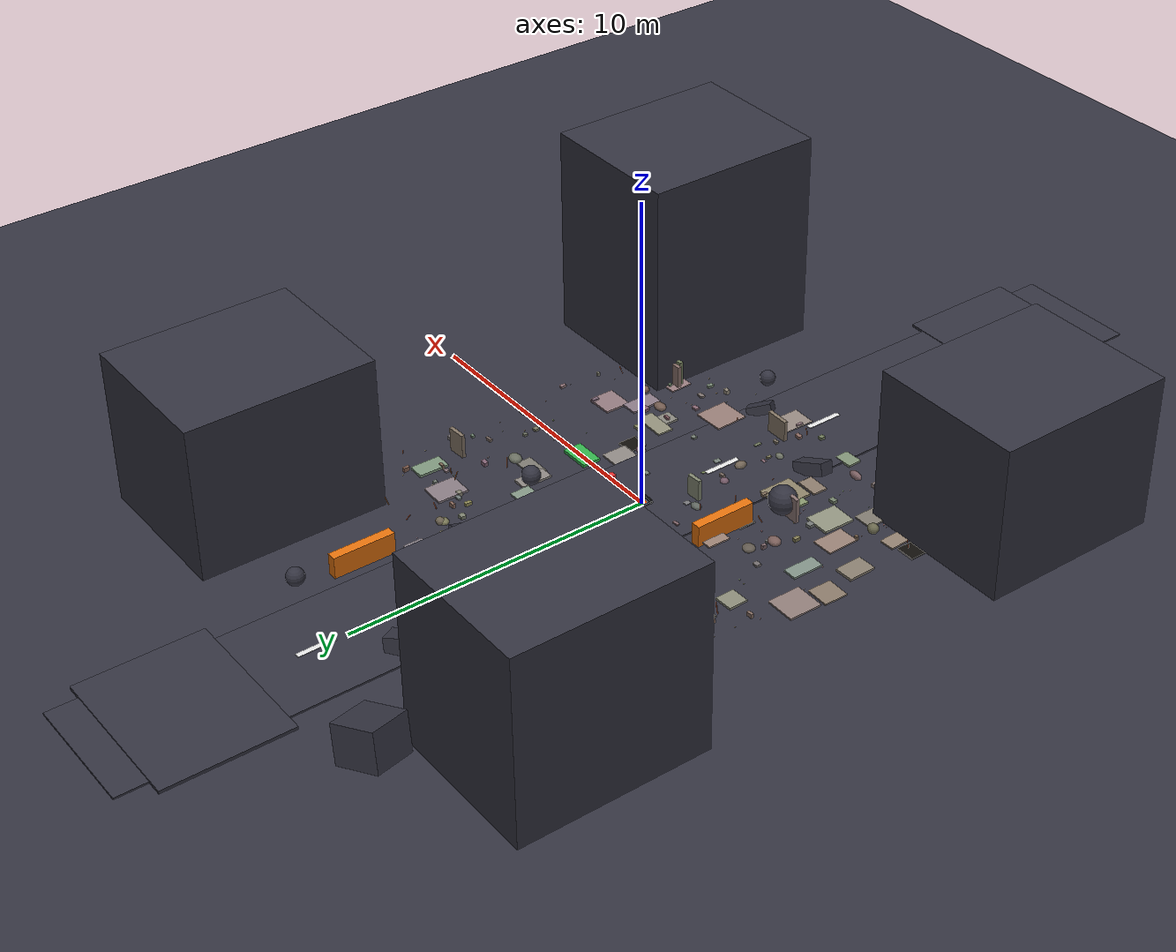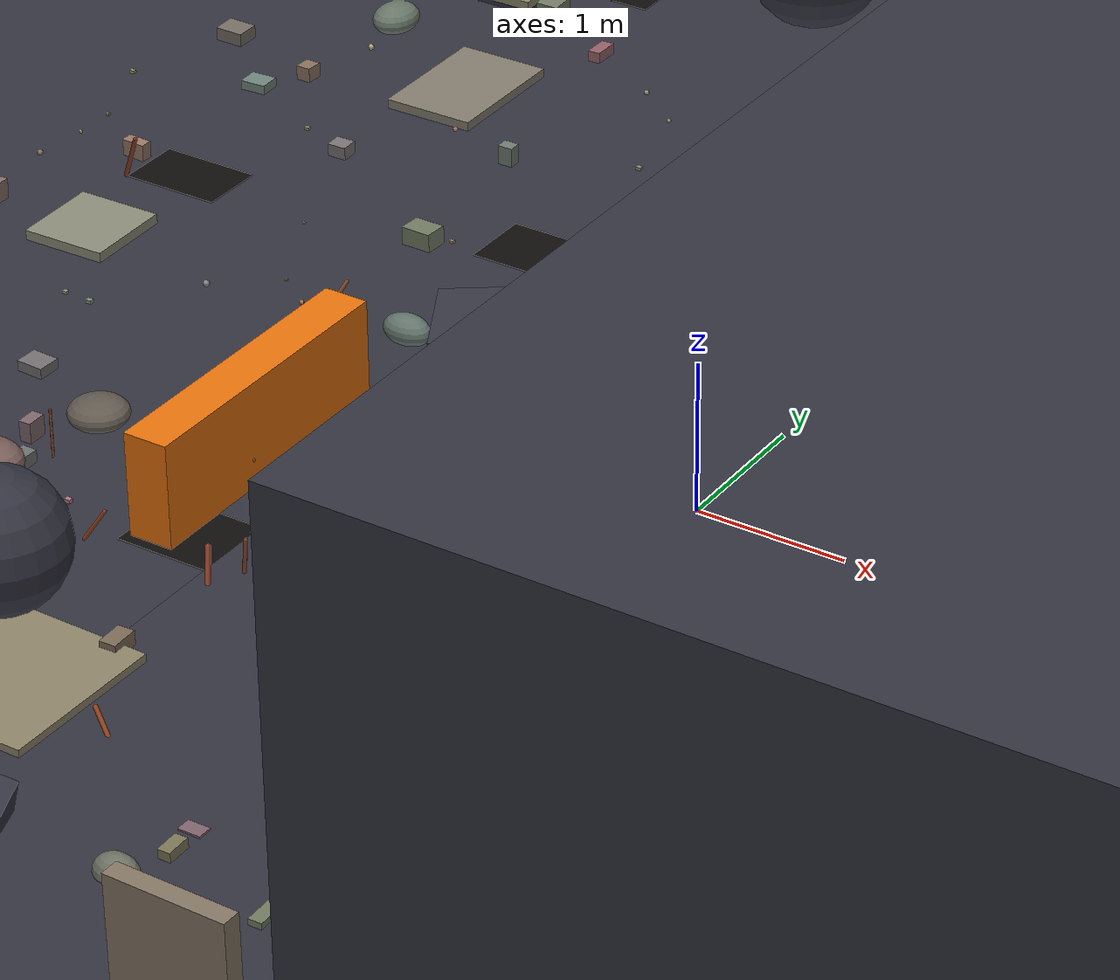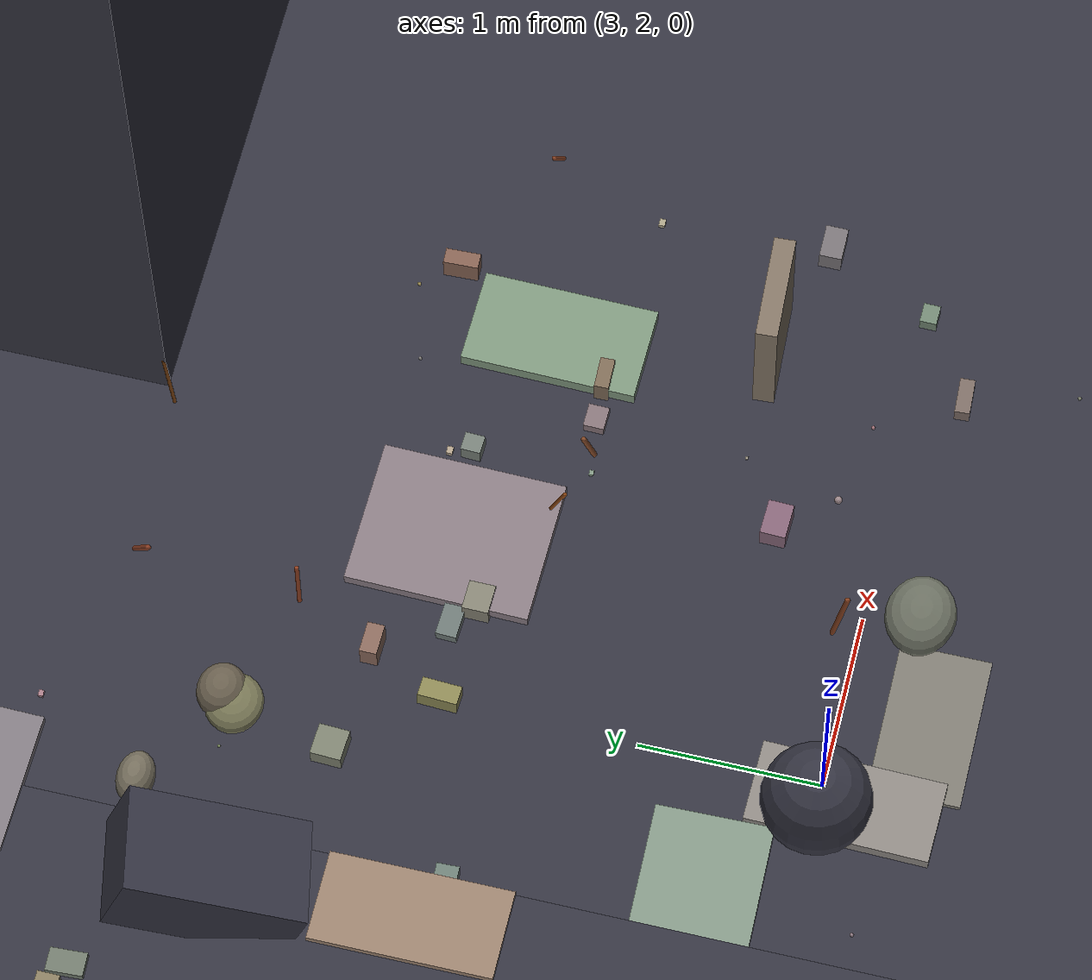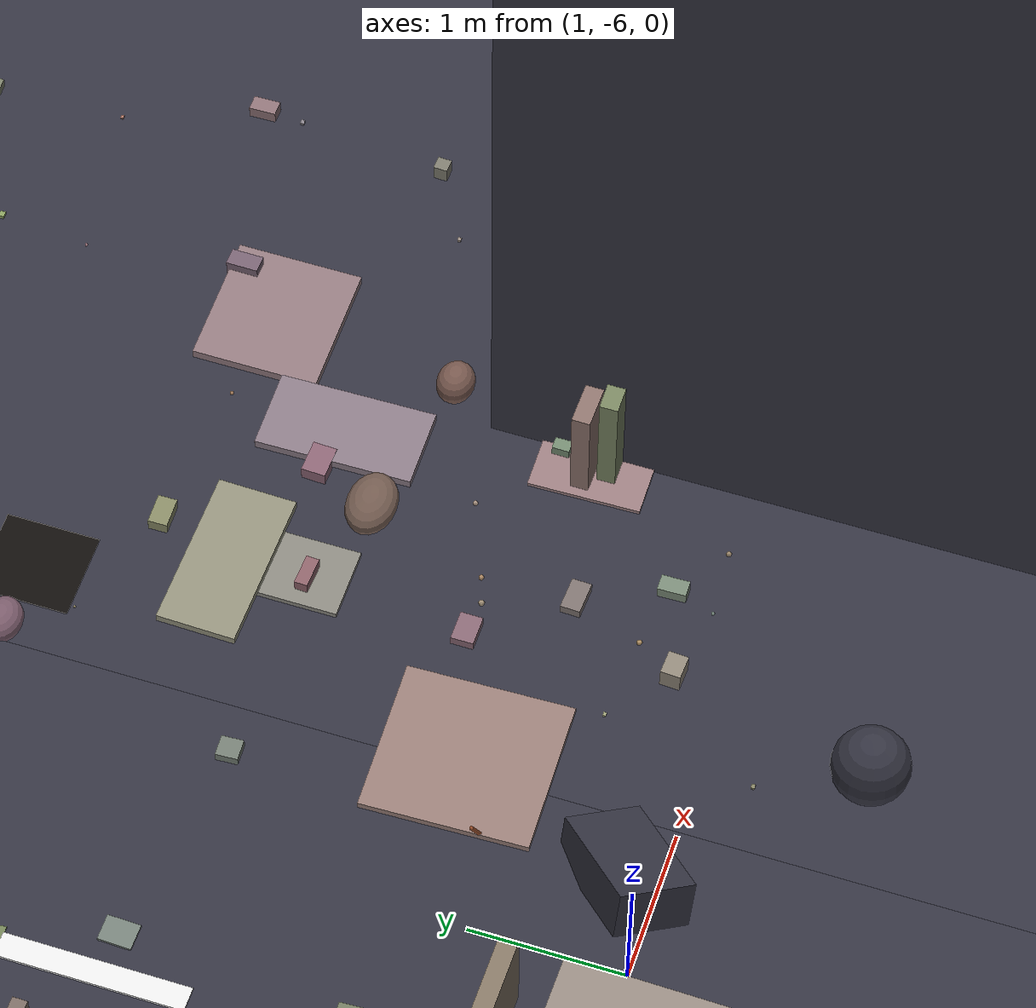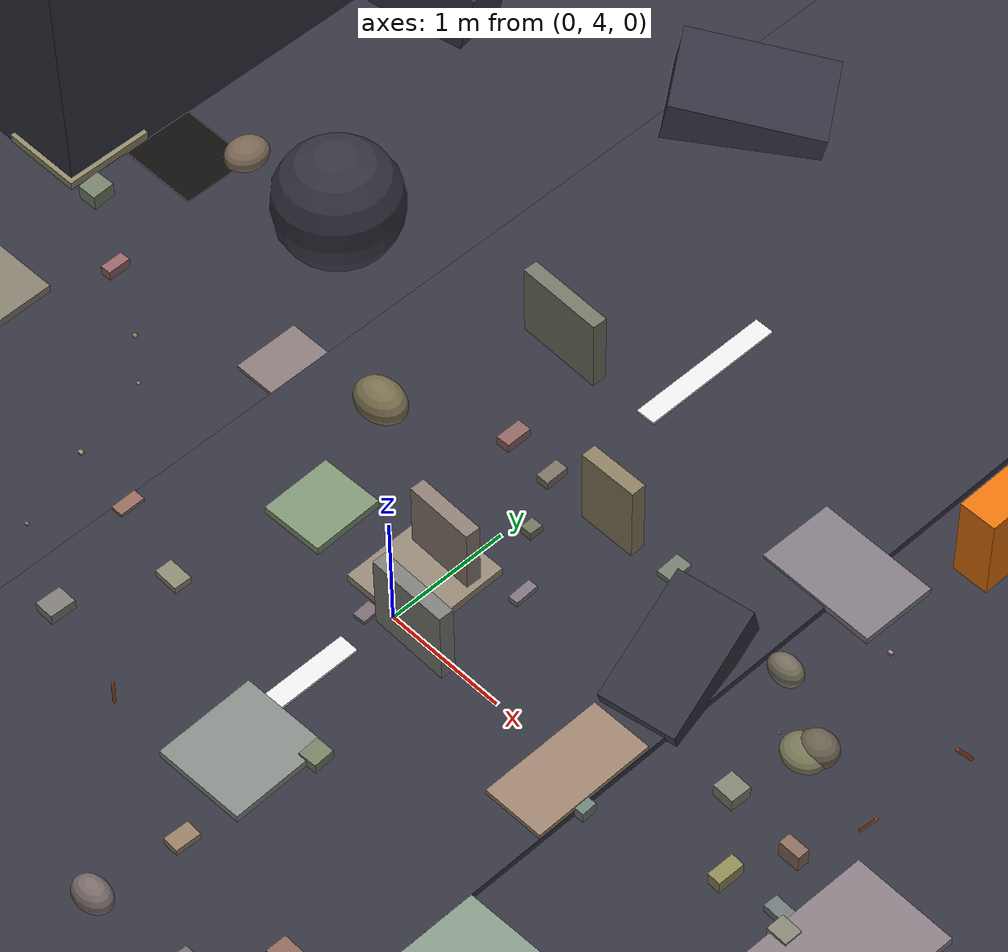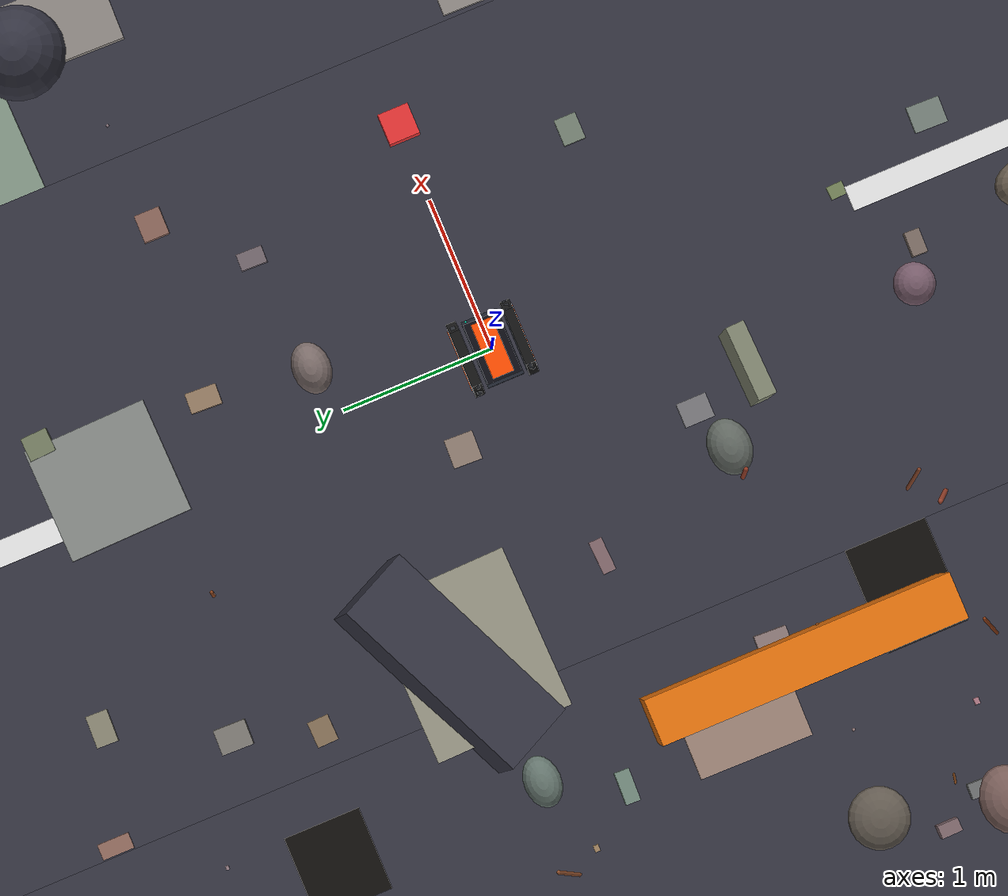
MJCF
<mujoco model="full_world">
    <option timestep="0.002" gravity="0 0 -9.81"/>

    <asset>
        <texture name="dusttex" type="2d" builtin="flat" rgb1="0.55 0.5 0.42" random="0.03" width="300" height="300"/>
        <texture name="sky"
                 type="skybox"
                 builtin="gradient"
                 rgb1="0.35 0.55 0.75"
                 rgb2="0.85 0.90 1.0"
                 width="512"
                 height="512"/>

        <material name="ground_mat"
                  texture="dusttex"
                  texrepeat="20 20"
                  rgba="0.5 0.48 0.42 1"
                  reflectance="0.05"/>

        <material name="road_mat"
                  rgba="0.12 0.12 0.14 1"/>

        <material name="path_mat"
                  rgba="0.55 0.55 0.50 1"/>

        <material name="rock_mat"
                  rgba="0.28 0.25 0.22 1"/>

        <material name="debris_mat"
                  rgba="0.45 0.40 0.35 1"/>

        <material name="wall_mat"
                  rgba="0.50 0.48 0.44 1"/>

        <material name="goal_mat"
                  rgba="0.15 0.65 0.20 1"/>

    </asset>

    <visual>
        <headlight diffuse="0.8 0.8 0.8"
                   ambient="0.3 0.3 0.3"
                   specular="0.1 0.1 0.1"/>
        <map znear="0.01" zfar="100"/>
    </visual>

    <worldbody>

        <!-- LIGHTS -->

        <light name="sun"
               pos="10 10 15"
               dir="-0.5 -0.5 -1"
               diffuse="0.8 0.8 0.8"
               ambient="0.3 0.3 0.3"/>

        <light name="fill"
               pos="-10 -10 8"
               dir="0.5 0.5 -1"
               diffuse="0.4 0.4 0.4"/>

        <!-- GROUND -->

        <geom name="ground"
              type="plane"
              size="30 30 0.1"
              material="ground_mat"
              friction="1 0.5 0.5"/>

        <!-- MAIN PATH -->

        <geom name="main_path"
              type="box"
              size="2 18 0.03"
              pos="0 0 0.03"
              material="path_mat"/>

        <geom name="start_area"
              type="box"
              size="2.5 2 0.04"
              pos="0 -15 0.04"
              material="road_mat"/>

        <geom name="goal_area"
              type="box"
              size="2.5 2 0.05"
              pos="0 15 0.05"
              material="goal_mat"/>

        <!-- PATH MARKERS -->

        <geom name="marker1" type="box" size="0.08 0.6 0.01" pos="0 -11 0.08" rgba="0.9 0.9 0.9 1"/>
        <geom name="marker2" type="box" size="0.08 0.6 0.01" pos="0 -7 0.08" rgba="0.9 0.9 0.9 1"/>
        <geom name="marker3" type="box" size="0.08 0.6 0.01" pos="0 -3 0.08" rgba="0.9 0.9 0.9 1"/>
        <geom name="marker4" type="box" size="0.08 0.6 0.01" pos="0 3 0.08" rgba="0.9 0.9 0.9 1"/>
        <geom name="marker5" type="box" size="0.08 0.6 0.01" pos="0 7 0.08" rgba="0.9 0.9 0.9 1"/>
        <geom name="marker6" type="box" size="0.08 0.6 0.01" pos="0 11 0.08" rgba="0.9 0.9 0.9 1"/>

        <!-- ROCKS -->

        <geom name="rock1" type="sphere" size="0.35" pos="-2.8 -10 0.35" material="rock_mat"/>
        <geom name="rock2" type="sphere" size="0.25" pos="2.7 -7 0.25" material="rock_mat"/>
        <geom name="rock3" type="sphere" size="0.45" pos="-2.8 -3 0.45" material="rock_mat"/>
        <geom name="rock4" type="sphere" size="0.30" pos="2.8 2 0.30" material="rock_mat"/>
        <geom name="rock5" type="sphere" size="0.50" pos="-2.7 6 0.50" material="rock_mat"/>
        <geom name="rock6" type="sphere" size="0.28" pos="2.8 10 0.28" material="rock_mat"/>

        <!-- DEBRIS -->

        <geom name="debris1" type="box" size="0.5 0.3 0.2" pos="-1.8 -5 0.2" euler="10 20 15" material="debris_mat"/>
        <geom name="debris2" type="box" size="0.4 0.25 0.15" pos="1.6 -5.8 0.15" euler="0 25 40" material="debris_mat"/>
        <geom name="debris3" type="box" size="0.7 0.25 0.18" pos="-1.7 1 0.18" euler="15 0 25" material="debris_mat"/>
        <geom name="debris4" type="box" size="0.3 0.5 0.2" pos="1.7 5 0.2" euler="20 10 10" material="debris_mat"/>
        <geom name="debris5" type="box" size="0.6 0.35 0.25" pos="-1.5 9 0.25" euler="5 15 35" material="debris_mat"/>

        <!-- COLLAPSED WALL -->

        <geom name="collapsed_wall1" type="box" size="1.5 0.25 0.5" pos="-5 8 0.5" euler="0 15 10" material="wall_mat"/>
        <geom name="collapsed_wall2" type="box" size="1.2 0.25 0.7" pos="-5 10 0.7" euler="10 0 -15" material="wall_mat"/>
        <geom name="collapsed_block" type="box" size="0.7 0.7 0.6" pos="-4.5 12 0.6" euler="5 15 20" material="debris_mat"/>

        <!-- BUILDING PLACEHOLDERS -->

        <geom name="building_left" type="box" size="2.5 3 2.5" pos="-7 -8 2.5" material="wall_mat"/>
        <geom name="building_right" type="box" size="2.5 3 3.5" pos="7 -7 3.5" material="wall_mat"/>
        <geom name="building_left_back" type="box" size="2.5 3 3" pos="-7 8 3" material="wall_mat"/>
        <geom name="building_right_back" type="box" size="2.5 3 2.5" pos="7 9 2.5" material="wall_mat"/>

        <!-- OBSTACLES -->

        <geom name="barrier1" type="box" size="0.15 1 0.35" pos="-2.5 -1 0.35" rgba="0.9 0.45 0.05 1"/>
        <geom name="barrier2" type="box" size="0.15 1 0.35" pos="2.5 8 0.35" rgba="0.9 0.45 0.05 1"/>

        <!-- Obstacles for Detection team to locate -->
        <geom name="obstacle_block" type="box" size="0.1 0.1 0.1" pos="1.5 0 0.1" rgba="0.9 0.2 0.2 1"/>
        <geom name="ramp" type="box" size="0.5 0.3 0.05" pos="3.0 0 0.05" rgba="0.2 0.7 0.3 1"/>

        <!-- ===== Collapsed-building debris field, scattered widely ===== -->
        <!-- Broken floor slabs: irregular size, random tilt AND yaw, some sunken -->
        <geom name="slab_0" type="box" pos="-2.29 -4.54 0.018" euler="-0.159 0.003 -1.452" size="0.43 0.24 0.031" rgba="0.542 0.478 0.421 1" friction="0.9 0.05 0.05"/>
        <geom name="slab_1" type="box" pos="-0.98 4.25 0.093" euler="0.028 -0.037 1.495" size="0.26 0.29 0.033" rgba="0.496 0.573 0.445 1" friction="0.9 0.05 0.05"/>
        <geom name="slab_2" type="box" pos="-4.62 -4.97 0.046" euler="0.05 -0.046 0.15" size="0.32 0.49 0.024" rgba="0.498 0.477 0.435 1" friction="0.9 0.05 0.05"/>
        <geom name="slab_3" type="box" pos="2.35 -0.94 0.009" euler="0.106 0.072 -0.804" size="0.32 0.41 0.029" rgba="0.559 0.533 0.515 1" friction="0.9 0.05 0.05"/>
        <geom name="slab_4" type="box" pos="2.98 -2.76 0.068" euler="-0.125 -0.004 -1.447" size="0.54 0.26 0.028" rgba="0.570 0.562 0.479 1" friction="0.9 0.05 0.05"/>
        <geom name="slab_5" type="box" pos="4.88 -2.42 0.029" euler="0.122 0.16 -0.081" size="0.45 0.42 0.032" rgba="0.570 0.477 0.494 1" friction="0.9 0.05 0.05"/>
        <geom name="slab_6" type="box" pos="1.91 6.41 0.057" euler="-0.172 -0.014 -1.042" size="0.49 0.31 0.028" rgba="0.504 0.477 0.502 1" friction="0.9 0.05 0.05"/>
        <geom name="slab_7" type="box" pos="-4.82 -3.28 0.028" euler="0.018 0.138 1.003" size="0.35 0.51 0.022" rgba="0.594 0.503 0.460 1" friction="0.9 0.05 0.05"/>
        <geom name="slab_8" type="box" pos="-1.84 4.99 0.0" euler="-0.096 -0.005 0.28" size="0.54 0.27 0.024" rgba="0.522 0.470 0.460 1" friction="0.9 0.05 0.05"/>
        <geom name="slab_9" type="box" pos="-1.7 0.86 0.05" euler="0.063 -0.161 1.255" size="0.53 0.45 0.03" rgba="0.584 0.575 0.506 1" friction="0.9 0.05 0.05"/>
        <geom name="slab_10" type="box" pos="-1.4 -1.31 -0.021" euler="-0.105 -0.122 -0.502" size="0.25 0.43 0.021" rgba="0.496 0.470 0.428 1" friction="0.9 0.05 0.05"/>
        <geom name="slab_11" type="box" pos="-5.18 -1.77 -0.011" euler="-0.089 -0.055 -0.427" size="0.23 0.51 0.032" rgba="0.505 0.572 0.529 1" friction="0.9 0.05 0.05"/>
        <geom name="slab_12" type="box" pos="-0.44 -0.21 0.004" euler="0.118 -0.122 -1.497" size="0.25 0.25 0.027" rgba="0.604 0.533 0.428 1" friction="0.9 0.05 0.05"/>
        <geom name="slab_13" type="box" pos="0.56 -6.15 0.061" euler="-0.086 -0.048 -1.045" size="0.39 0.54 0.037" rgba="0.583 0.534 0.503 1" friction="0.9 0.05 0.05"/>
        <geom name="slab_14" type="box" pos="-2.21 -3.6 0.075" euler="0.115 0.086 -0.858" size="0.49 0.55 0.037" rgba="0.552 0.513 0.413 1" friction="0.9 0.05 0.05"/>
        <geom name="slab_15" type="box" pos="-6.14 -2.87 0.028" euler="0.157 0.176 1.429" size="0.31 0.45 0.039" rgba="0.534 0.496 0.437 1" friction="0.9 0.05 0.05"/>
        <geom name="slab_16" type="box" pos="-3.94 -3.84 0.032" euler="0.055 0.108 -1.304" size="0.43 0.52 0.037" rgba="0.569 0.579 0.504 1" friction="0.9 0.05 0.05"/>
        <geom name="slab_17" type="box" pos="-4.18 3.76 0.021" euler="-0.036 0.161 0.706" size="0.33 0.48 0.039" rgba="0.510 0.485 0.428 1" friction="0.9 0.05 0.05"/>
        <geom name="slab_18" type="box" pos="5.26 3.98 0.055" euler="-0.054 0.018 -1.159" size="0.27 0.49 0.04" rgba="0.492 0.587 0.488 1" friction="0.9 0.05 0.05"/>
        <geom name="slab_19" type="box" pos="0.35 5.64 -0.003" euler="-0.089 -0.075 -0.815" size="0.36 0.51 0.037" rgba="0.560 0.501 0.460 1" friction="0.9 0.05 0.05"/>
        <geom name="slab_20" type="box" pos="-4.8 5.33 0.088" euler="-0.029 0.15 0.005" size="0.34 0.37 0.032" rgba="0.554 0.533 0.412 1" friction="0.9 0.05 0.05"/>
        <geom name="slab_21" type="box" pos="-0.78 -4.12 0.032" euler="0.081 0.02 -0.546" size="0.22 0.48 0.023" rgba="0.552 0.537 0.504 1" friction="0.9 0.05 0.05"/>
        <geom name="slab_22" type="box" pos="-5.12 0.78 0.036" euler="0.022 0.094 1.295" size="0.3 0.31 0.035" rgba="0.543 0.544 0.471 1" friction="0.9 0.05 0.05"/>
        <geom name="slab_23" type="box" pos="0.16 2.51 0.092" euler="0.072 0.136 1.388" size="0.37 0.4 0.03" rgba="0.521 0.537 0.523 1" friction="0.9 0.05 0.05"/>
        <geom name="slab_24" type="box" pos="4.42 -4.72 0.001" euler="-0.154 0.061 0.892" size="0.26 0.37 0.021" rgba="0.598 0.489 0.496 1" friction="0.9 0.05 0.05"/>
        <geom name="slab_25" type="box" pos="2.08 -4.64 0.094" euler="-0.037 -0.005 1.538" size="0.51 0.54 0.024" rgba="0.590 0.489 0.462 1" friction="0.9 0.05 0.05"/>
        <geom name="slab_26" type="box" pos="0.2 -2.09 -0.027" euler="0.019 -0.021 -1.513" size="0.28 0.33 0.034" rgba="0.530 0.545 0.471 1" friction="0.9 0.05 0.05"/>
        <geom name="slab_27" type="box" pos="-5.66 6.31 0.005" euler="-0.166 0.1 -0.721" size="0.48 0.54 0.022" rgba="0.506 0.521 0.519 1" friction="0.9 0.05 0.05"/>
        <geom name="slab_28" type="box" pos="4.15 -3.14 0.061" euler="-0.148 -0.159 0.591" size="0.27 0.52 0.031" rgba="0.541 0.479 0.523 1" friction="0.9 0.05 0.05"/>
        <geom name="slab_29" type="box" pos="1.75 3.92 0.082" euler="-0.017 -0.058 0.167" size="0.25 0.5 0.021" rgba="0.601 0.502 0.426 1" friction="0.9 0.05 0.05"/>
        <geom name="slab_30" type="box" pos="0.35 -3.4 -0.004" euler="-0.068 -0.07 0.815" size="0.26 0.27 0.021" rgba="0.525 0.530 0.431 1" friction="0.9 0.05 0.05"/>
        <geom name="slab_31" type="box" pos="-1.99 -6.26 0.042" euler="-0.112 -0.009 1.365" size="0.3 0.23 0.035" rgba="0.503 0.568 0.462 1" friction="0.9 0.05 0.05"/>
        <geom name="slab_32" type="box" pos="-0.06 4.35 0.098" euler="-0.057 0.12 0.649" size="0.35 0.39 0.034" rgba="0.566 0.519 0.452 1" friction="0.9 0.05 0.05"/>
        <geom name="slab_33" type="box" pos="-5.79 -4.81 -0.009" euler="-0.15 0.123 1.163" size="0.24 0.46 0.025" rgba="0.570 0.504 0.439 1" friction="0.9 0.05 0.05"/>
        <geom name="slab_34" type="box" pos="-2.69 -0.53 0.095" euler="0.17 0.017 -0.802" size="0.27 0.37 0.025" rgba="0.606 0.507 0.453 1" friction="0.9 0.05 0.05"/>
        <geom name="slab_35" type="box" pos="-6.49 -1.54 0.036" euler="-0.178 -0.085 -1.288" size="0.38 0.39 0.024" rgba="0.538 0.475 0.413 1" friction="0.9 0.05 0.05"/>
        <geom name="slab_36" type="box" pos="-2.54 -3.47 0.055" euler="0.078 0.136 -0.347" size="0.41 0.39 0.035" rgba="0.529 0.588 0.428 1" friction="0.9 0.05 0.05"/>
        <geom name="slab_37" type="box" pos="2.91 1.86 0.052" euler="0.084 0.112 -1.133" size="0.23 0.5 0.038" rgba="0.553 0.531 0.510 1" friction="0.9 0.05 0.05"/>
        <geom name="slab_38" type="box" pos="3.96 4.24 0.06" euler="-0.097 -0.169 -1.152" size="0.41 0.51 0.034" rgba="0.533 0.483 0.510 1" friction="0.9 0.05 0.05"/>
        <geom name="slab_39" type="box" pos="0.76 1.66 -0.03" euler="0.107 0.089 0.009" size="0.43 0.44 0.03" rgba="0.554 0.549 0.418 1" friction="0.9 0.05 0.05"/>
        <geom name="slab_40" type="box" pos="3.08 -3.22 -0.003" euler="0.086 0.171 -0.019" size="0.24 0.31 0.035" rgba="0.536 0.527 0.492 1" friction="0.9 0.05 0.05"/>
        <geom name="slab_41" type="box" pos="3.47 1.52 0.003" euler="0.088 -0.07 0.213" size="0.43 0.25 0.023" rgba="0.491 0.477 0.442 1" friction="0.9 0.05 0.05"/>
        <geom name="slab_42" type="box" pos="2.24 2.5 0.03" euler="-0.012 -0.137 1.236" size="0.44 0.32 0.03" rgba="0.514 0.587 0.522 1" friction="0.9 0.05 0.05"/>
        <geom name="slab_43" type="box" pos="-6.27 -0.53 0.005" euler="-0.104 0.16 -0.908" size="0.49 0.54 0.029" rgba="0.560 0.487 0.473 1" friction="0.9 0.05 0.05"/>
        <geom name="slab_44" type="box" pos="5.89 -4.78 0.061" euler="-0.097 0.143 -0.044" size="0.49 0.39 0.038" rgba="0.493 0.470 0.469 1" friction="0.9 0.05 0.05"/>
        <!-- Big broken concrete boulders -->
        <geom name="boulder_0" type="ellipsoid" pos="-0.64 -2.57 0.067" euler="1.021 -1.495 0.752" size="0.137 0.134 0.112" rgba="0.461 0.354 0.411 1"/>
        <geom name="boulder_1" type="ellipsoid" pos="2.77 5.22 0.071" euler="1.496 0.268 -0.418" size="0.155 0.137 0.118" rgba="0.411 0.373 0.306 1"/>
        <geom name="boulder_2" type="ellipsoid" pos="-5.18 4.35 0.064" euler="-0.703 0.033 -0.93" size="0.154 0.194 0.107" rgba="0.405 0.455 0.406 1"/>
        <geom name="boulder_3" type="ellipsoid" pos="4.06 1.7 0.077" euler="0.659 -1.352 0.697" size="0.23 0.194 0.128" rgba="0.414 0.430 0.377 1"/>
        <geom name="boulder_4" type="ellipsoid" pos="-2.78 -5.86 0.074" euler="-0.469 -0.607 0.717" size="0.231 0.113 0.123" rgba="0.477 0.371 0.379 1"/>
        <geom name="boulder_5" type="ellipsoid" pos="-2.59 0.75 0.061" euler="-0.876 1.218 -0.009" size="0.167 0.117 0.101" rgba="0.386 0.449 0.420 1"/>
        <geom name="boulder_6" type="ellipsoid" pos="-0.65 -4.69 0.068" euler="-1.227 -0.783 -0.725" size="0.143 0.109 0.114" rgba="0.428 0.446 0.390 1"/>
        <geom name="boulder_7" type="ellipsoid" pos="-1.13 -1.12 0.068" euler="-1.314 -0.667 1.403" size="0.183 0.138 0.114" rgba="0.375 0.400 0.376 1"/>
        <geom name="boulder_8" type="ellipsoid" pos="4.72 -3.69 0.071" euler="-0.162 1.362 1.046" size="0.153 0.125 0.118" rgba="0.465 0.343 0.304 1"/>
        <geom name="boulder_9" type="ellipsoid" pos="2.72 5.14 0.054" euler="-0.325 1.28 0.977" size="0.177 0.159 0.09" rgba="0.463 0.457 0.330 1"/>
        <geom name="boulder_10" type="ellipsoid" pos="-5.08 -4.49 0.094" euler="0.665 0.442 0.794" size="0.183 0.168 0.156" rgba="0.415 0.406 0.305 1"/>
        <geom name="boulder_11" type="ellipsoid" pos="3.67 -3.48 0.067" euler="-1.116 -0.745 0.409" size="0.23 0.165 0.111" rgba="0.444 0.353 0.308 1"/>
        <geom name="boulder_12" type="ellipsoid" pos="0.32 1.08 0.079" euler="-1.469 -0.595 -0.118" size="0.167 0.122 0.132" rgba="0.475 0.417 0.406 1"/>
        <geom name="boulder_13" type="ellipsoid" pos="-0.32 -3.45 0.083" euler="-0.578 -1.435 -0.005" size="0.15 0.196 0.139" rgba="0.441 0.390 0.331 1"/>
        <geom name="boulder_14" type="ellipsoid" pos="2.18 5.53 0.068" euler="-0.238 0.548 -0.906" size="0.147 0.103 0.114" rgba="0.456 0.429 0.361 1"/>
        <geom name="boulder_15" type="ellipsoid" pos="-3.83 6.11 0.064" euler="-0.836 0.781 -0.615" size="0.157 0.182 0.106" rgba="0.474 0.399 0.322 1"/>
        <geom name="boulder_16" type="ellipsoid" pos="-3.6 -1.08 0.06" euler="-0.32 -0.861 1.422" size="0.2 0.195 0.1" rgba="0.377 0.346 0.307 1"/>
        <geom name="boulder_17" type="ellipsoid" pos="-1.39 5.18 0.096" euler="1.295 -0.512 -0.943" size="0.226 0.173 0.16" rgba="0.472 0.430 0.304 1"/>
        <geom name="boulder_18" type="ellipsoid" pos="2.14 -1.58 0.061" euler="-1.491 -0.661 -0.446" size="0.165 0.133 0.102" rgba="0.475 0.355 0.416 1"/>
        <geom name="boulder_19" type="ellipsoid" pos="-3.8 -1.86 0.072" euler="-1.352 -0.08 -0.382" size="0.219 0.182 0.12" rgba="0.470 0.363 0.344 1"/>
        <!-- Medium rubble chunks -->
        <geom name="chunk_0" type="box" pos="5.16 -6.11 0.068" euler="-1.378 -1.395 -2.747" size="0.069 0.097 0.068" rgba="0.567 0.421 0.440 1"/>
        <geom name="chunk_1" type="box" pos="5.18 -2.09 0.061" euler="-0.713 0.65 -1.152" size="0.059 0.107 0.061" rgba="0.464 0.381 0.441 1"/>
        <geom name="chunk_2" type="box" pos="5.41 1.74 0.042" euler="-0.074 1.37 2.851" size="0.106 0.042 0.042" rgba="0.482 0.420 0.389 1"/>
        <geom name="chunk_3" type="box" pos="-0.08 5.57 0.067" euler="0.968 0.818 0.674" size="0.053 0.096 0.067" rgba="0.472 0.431 0.378 1"/>
        <geom name="chunk_4" type="box" pos="3.67 -5.47 0.042" euler="-1.306 -1.398 0.33" size="0.054 0.093 0.042" rgba="0.472 0.537 0.461 1"/>
        <geom name="chunk_5" type="box" pos="6.34 -3.06 0.055" euler="0.629 -0.159 -1.669" size="0.046 0.047 0.055" rgba="0.487 0.479 0.428 1"/>
        <geom name="chunk_6" type="box" pos="3.22 4.51 0.072" euler="-0.619 0.201 -0.798" size="0.087 0.048 0.072" rgba="0.538 0.412 0.360 1"/>
        <geom name="chunk_7" type="box" pos="-3.31 -4.51 0.046" euler="-0.312 1.477 0.046" size="0.102 0.08 0.046" rgba="0.457 0.509 0.425 1"/>
        <geom name="chunk_8" type="box" pos="6.38 -5.17 0.072" euler="1.243 -1.379 -1.296" size="0.073 0.097 0.072" rgba="0.439 0.410 0.476 1"/>
        <geom name="chunk_9" type="box" pos="1.08 5.59 0.052" euler="-0.72 0.833 2.799" size="0.066 0.101 0.052" rgba="0.437 0.475 0.419 1"/>
        <geom name="chunk_10" type="box" pos="-3.67 -1.71 0.043" euler="0.298 0.455 -1.862" size="0.05 0.054 0.043" rgba="0.422 0.432 0.429 1"/>
        <geom name="chunk_11" type="box" pos="-4.09 -2.44 0.057" euler="-1.31 -1.196 -0.658" size="0.054 0.096 0.057" rgba="0.508 0.482 0.335 1"/>
        <geom name="chunk_12" type="box" pos="-4.37 2.54 0.045" euler="1.36 -0.563 0.418" size="0.069 0.06 0.045" rgba="0.477 0.447 0.458 1"/>
        <geom name="chunk_13" type="box" pos="6.46 -1.77 0.04" euler="-1.482 1.205 -0.479" size="0.054 0.091 0.04" rgba="0.551 0.445 0.461 1"/>
        <geom name="chunk_14" type="box" pos="-0.51 -4.39 0.062" euler="1.229 -1.233 0.767" size="0.041 0.079 0.062" rgba="0.479 0.461 0.343 1"/>
        <geom name="chunk_15" type="box" pos="-2.82 0.28 0.055" euler="0.914 1.401 -1.901" size="0.105 0.048 0.055" rgba="0.440 0.531 0.476 1"/>
        <geom name="chunk_16" type="box" pos="-0.22 -5.81 0.075" euler="0.361 0.974 -2.133" size="0.105 0.067 0.075" rgba="0.546 0.416 0.385 1"/>
        <geom name="chunk_17" type="box" pos="4.5 4.28 0.05" euler="0.054 -0.349 -2.367" size="0.053 0.055 0.05" rgba="0.460 0.496 0.464 1"/>
        <geom name="chunk_18" type="box" pos="-5.97 0.81 0.072" euler="-1.147 0.299 0.314" size="0.093 0.043 0.072" rgba="0.520 0.429 0.387 1"/>
        <geom name="chunk_19" type="box" pos="1.07 -0.97 0.052" euler="-1.43 0.357 -0.066" size="0.086 0.071 0.052" rgba="0.458 0.502 0.445 1"/>
        <geom name="chunk_20" type="box" pos="-0.54 -4.17 0.036" euler="-0.208 -1.225 -0.364" size="0.073 0.047 0.036" rgba="0.502 0.387 0.422 1"/>
        <geom name="chunk_21" type="box" pos="-5.43 3.04 0.033" euler="0.012 -0.366 2.831" size="0.094 0.076 0.033" rgba="0.442 0.517 0.479 1"/>
        <geom name="chunk_22" type="box" pos="3.02 4.09 0.055" euler="1.37 1.248 -2.103" size="0.054 0.109 0.055" rgba="0.546 0.529 0.330 1"/>
        <geom name="chunk_23" type="box" pos="-1.94 3.33 0.044" euler="0.947 -1.069 0.014" size="0.051 0.103 0.044" rgba="0.567 0.413 0.362 1"/>
        <geom name="chunk_24" type="box" pos="0.08 -2.35 0.038" euler="1.309 0.539 2.483" size="0.043 0.053 0.038" rgba="0.447 0.506 0.338 1"/>
        <geom name="chunk_25" type="box" pos="0.4 1.77 0.058" euler="0.24 1.148 -2.483" size="0.065 0.101 0.058" rgba="0.579 0.481 0.383 1"/>
        <geom name="chunk_26" type="box" pos="3.87 -3.06 0.048" euler="0.794 -0.173 -2.03" size="0.109 0.08 0.048" rgba="0.539 0.388 0.451 1"/>
        <geom name="chunk_27" type="box" pos="-3.2 1.81 0.063" euler="-0.562 -1.495 -2.928" size="0.109 0.081 0.063" rgba="0.444 0.479 0.389 1"/>
        <geom name="chunk_28" type="box" pos="0.16 5.14 0.063" euler="-1.433 -1.492 -0.911" size="0.049 0.056 0.063" rgba="0.437 0.437 0.356 1"/>
        <geom name="chunk_29" type="box" pos="1.09 1.16 0.054" euler="-1.096 1.31 -1.61" size="0.054 0.084 0.054" rgba="0.444 0.395 0.422 1"/>
        <geom name="chunk_30" type="box" pos="4.83 3.67 0.031" euler="0.435 0.187 -0.94" size="0.068 0.058 0.031" rgba="0.523 0.451 0.470 1"/>
        <geom name="chunk_31" type="box" pos="3.04 -3.27 0.057" euler="-0.282 -0.787 -2.773" size="0.103 0.043 0.057" rgba="0.545 0.382 0.408 1"/>
        <geom name="chunk_32" type="box" pos="5.73 -4.65 0.055" euler="0.425 0.94 -2.043" size="0.054 0.083 0.055" rgba="0.470 0.428 0.328 1"/>
        <geom name="chunk_33" type="box" pos="5.06 3.68 0.072" euler="0.736 -0.104 1.518" size="0.09 0.04 0.072" rgba="0.492 0.416 0.337 1"/>
        <geom name="chunk_34" type="box" pos="-3.48 -6.0 0.065" euler="1.036 0.635 -1.47" size="0.063 0.092 0.065" rgba="0.509 0.450 0.446 1"/>
        <geom name="chunk_35" type="box" pos="0.3 -3.05 0.041" euler="1.14 -1.454 -1.505" size="0.085 0.108 0.041" rgba="0.458 0.499 0.471 1"/>
        <geom name="chunk_36" type="box" pos="3.2 -2.25 0.042" euler="1.223 0.392 1.211" size="0.102 0.063 0.042" rgba="0.526 0.537 0.395 1"/>
        <geom name="chunk_37" type="box" pos="4.42 2.57 0.066" euler="0.211 -0.577 -1.809" size="0.1 0.071 0.066" rgba="0.520 0.392 0.466 1"/>
        <geom name="chunk_38" type="box" pos="-4.62 -6.15 0.047" euler="-1.074 -1.414 -2.878" size="0.047 0.105 0.047" rgba="0.531 0.481 0.432 1"/>
        <geom name="chunk_39" type="box" pos="3.08 -5.65 0.071" euler="0.959 1.174 -2.726" size="0.081 0.065 0.071" rgba="0.559 0.526 0.471 1"/>
        <geom name="chunk_40" type="box" pos="-5.11 -3.83 0.072" euler="0.936 0.403 2.041" size="0.048 0.042 0.072" rgba="0.521 0.426 0.336 1"/>
        <geom name="chunk_41" type="box" pos="-5.23 3.35 0.051" euler="-1.437 -0.73 -1.365" size="0.054 0.062 0.051" rgba="0.535 0.439 0.371 1"/>
        <geom name="chunk_42" type="box" pos="6.03 0.05 0.032" euler="-0.261 -0.191 1.715" size="0.1 0.083 0.032" rgba="0.475 0.493 0.406 1"/>
        <geom name="chunk_43" type="box" pos="-3.68 4.71 0.039" euler="-1.496 -0.894 1.646" size="0.046 0.097 0.039" rgba="0.576 0.381 0.399 1"/>
        <geom name="chunk_44" type="box" pos="-0.11 3.86 0.047" euler="0.996 -0.718 2.788" size="0.053 0.075 0.047" rgba="0.465 0.414 0.432 1"/>
        <geom name="chunk_45" type="box" pos="-0.02 -5.07 0.069" euler="0.591 0.861 0.803" size="0.085 0.046 0.069" rgba="0.477 0.444 0.383 1"/>
        <geom name="chunk_46" type="box" pos="5.08 -5.38 0.04" euler="-0.71 1.204 0.007" size="0.102 0.042 0.04" rgba="0.481 0.521 0.357 1"/>
        <geom name="chunk_47" type="box" pos="-0.51 0.41 0.062" euler="-0.455 -0.52 -2.165" size="0.093 0.093 0.062" rgba="0.555 0.486 0.439 1"/>
        <geom name="chunk_48" type="box" pos="-4.3 -0.8 0.036" euler="-0.114 1.155 -1.646" size="0.094 0.081 0.036" rgba="0.451 0.428 0.433 1"/>
        <geom name="chunk_49" type="box" pos="4.47 -4.49 0.046" euler="0.067 -1.017 -1.08" size="0.051 0.057 0.046" rgba="0.450 0.536 0.437 1"/>
        <geom name="chunk_50" type="box" pos="-5.18 6.01 0.079" euler="0.885 0.7 -0.409" size="0.047 0.067 0.079" rgba="0.451 0.482 0.337 1"/>
        <geom name="chunk_51" type="box" pos="-3.82 -1.45 0.07" euler="0.58 0.001 0.831" size="0.042 0.068 0.07" rgba="0.494 0.403 0.417 1"/>
        <geom name="chunk_52" type="box" pos="-1.24 3.13 0.059" euler="0.747 -0.237 -1.705" size="0.104 0.07 0.059" rgba="0.536 0.521 0.444 1"/>
        <geom name="chunk_53" type="box" pos="2.6 4.58 0.053" euler="-0.561 0.385 -2.525" size="0.088 0.085 0.053" rgba="0.487 0.505 0.434 1"/>
        <geom name="chunk_54" type="box" pos="1.68 -3.25 0.061" euler="-0.272 0.526 2.702" size="0.07 0.072 0.061" rgba="0.449 0.485 0.445 1"/>
        <geom name="chunk_55" type="box" pos="-1.45 -0.13 0.057" euler="-1.017 0.845 2.767" size="0.108 0.043 0.057" rgba="0.503 0.396 0.412 1"/>
        <geom name="chunk_56" type="box" pos="0.53 2.82 0.071" euler="0.065 -0.269 2.813" size="0.076 0.085 0.071" rgba="0.454 0.489 0.383 1"/>
        <geom name="chunk_57" type="box" pos="3.42 -4.91 0.033" euler="-0.677 -0.301 -3.056" size="0.109 0.065 0.033" rgba="0.487 0.447 0.432 1"/>
        <geom name="chunk_58" type="box" pos="-1.92 -3.05 0.077" euler="0.081 -0.843 1.893" size="0.056 0.092 0.077" rgba="0.483 0.414 0.341 1"/>
        <geom name="chunk_59" type="box" pos="3.6 4.02 0.058" euler="-0.822 1.392 -0.922" size="0.084 0.073 0.058" rgba="0.522 0.511 0.451 1"/>
        <geom name="chunk_60" type="box" pos="-0.41 -2.67 0.072" euler="-0.436 1.052 -1.461" size="0.078 0.049 0.072" rgba="0.480 0.421 0.388 1"/>
        <geom name="chunk_61" type="box" pos="-4.08 -6.46 0.042" euler="-0.595 -0.061 -0.449" size="0.091 0.06 0.042" rgba="0.522 0.485 0.378 1"/>
        <geom name="chunk_62" type="box" pos="5.57 4.61 0.075" euler="0.852 -1.079 2.081" size="0.044 0.098 0.075" rgba="0.521 0.382 0.322 1"/>
        <geom name="chunk_63" type="box" pos="5.87 2.03 0.037" euler="-0.799 0.829 -0.964" size="0.058 0.047 0.037" rgba="0.444 0.525 0.447 1"/>
        <geom name="chunk_64" type="box" pos="-4.32 5.08 0.063" euler="1.182 0.864 2.128" size="0.083 0.095 0.063" rgba="0.452 0.491 0.405 1"/>
        <geom name="chunk_65" type="box" pos="4.97 0.72 0.037" euler="-0.021 -1.325 -0.207" size="0.059 0.056 0.037" rgba="0.443 0.459 0.400 1"/>
        <geom name="chunk_66" type="box" pos="0.51 4.72 0.053" euler="0.188 0.496 2.139" size="0.04 0.099 0.053" rgba="0.480 0.447 0.474 1"/>
        <geom name="chunk_67" type="box" pos="-5.52 1.78 0.06" euler="0.548 1.294 -1.065" size="0.085 0.042 0.06" rgba="0.577 0.462 0.398 1"/>
        <geom name="chunk_68" type="box" pos="5.17 -6.06 0.047" euler="1.085 -0.402 -0.16" size="0.09 0.084 0.047" rgba="0.504 0.503 0.354 1"/>
        <geom name="chunk_69" type="box" pos="-0.84 -1.01 0.045" euler="0.983 -0.289 0.024" size="0.079 0.098 0.045" rgba="0.463 0.461 0.476 1"/>
        <geom name="chunk_70" type="box" pos="2.01 3.8 0.045" euler="0.259 0.404 1.785" size="0.063 0.062 0.045" rgba="0.426 0.496 0.462 1"/>
        <geom name="chunk_71" type="box" pos="0.59 -5.85 0.039" euler="1.264 0.326 0.992" size="0.061 0.04 0.039" rgba="0.546 0.526 0.418 1"/>
        <geom name="chunk_72" type="box" pos="1.52 1.65 0.064" euler="-0.862 0.501 -0.265" size="0.089 0.082 0.064" rgba="0.542 0.396 0.349 1"/>
        <geom name="chunk_73" type="box" pos="-6.02 3.57 0.048" euler="0.968 0.86 0.39" size="0.104 0.086 0.048" rgba="0.461 0.428 0.387 1"/>
        <geom name="chunk_74" type="box" pos="-2.36 -0.9 0.033" euler="0.203 -1.382 -2.394" size="0.085 0.105 0.033" rgba="0.550 0.472 0.467 1"/>
        <geom name="chunk_75" type="box" pos="-0.7 -6.32 0.077" euler="1.442 -0.074 -0.55" size="0.067 0.081 0.077" rgba="0.436 0.483 0.354 1"/>
        <geom name="chunk_76" type="box" pos="-4.53 -6.3 0.036" euler="1.399 -1.236 2.321" size="0.04 0.088 0.036" rgba="0.441 0.383 0.435 1"/>
        <geom name="chunk_77" type="box" pos="-3.35 3.04 0.069" euler="0.641 1.066 1.443" size="0.053 0.044 0.069" rgba="0.433 0.481 0.433 1"/>
        <geom name="chunk_78" type="box" pos="-0.51 5.62 0.066" euler="-1.466 -1.456 0.946" size="0.058 0.108 0.066" rgba="0.551 0.393 0.370 1"/>
        <geom name="chunk_79" type="box" pos="2.98 -4.34 0.033" euler="-0.397 0.225 -0.385" size="0.1 0.074 0.033" rgba="0.528 0.403 0.448 1"/>
        <geom name="chunk_80" type="box" pos="-1.78 1.88 0.049" euler="0.859 1.335 1.787" size="0.084 0.069 0.049" rgba="0.511 0.427 0.330 1"/>
        <geom name="chunk_81" type="box" pos="6.16 2.64 0.06" euler="1.432 0.994 0.635" size="0.098 0.063 0.06" rgba="0.469 0.449 0.462 1"/>
        <geom name="chunk_82" type="box" pos="-1.6 2.4 0.07" euler="-0.65 -1.495 -1.488" size="0.082 0.103 0.07" rgba="0.488 0.474 0.451 1"/>
        <geom name="chunk_83" type="box" pos="5.04 -5.95 0.073" euler="0.216 -0.678 2.205" size="0.098 0.097 0.073" rgba="0.549 0.490 0.466 1"/>
        <geom name="chunk_84" type="box" pos="-1.99 -5.39 0.04" euler="0.751 1.295 -1.67" size="0.079 0.096 0.04" rgba="0.517 0.488 0.394 1"/>
        <geom name="chunk_85" type="box" pos="-3.81 -3.19 0.053" euler="-1.237 0.92 1.709" size="0.093 0.095 0.053" rgba="0.457 0.473 0.464 1"/>
        <geom name="chunk_86" type="box" pos="5.01 0.28 0.039" euler="-0.923 -0.958 1.263" size="0.073 0.081 0.039" rgba="0.478 0.470 0.384 1"/>
        <geom name="chunk_87" type="box" pos="0.22 -4.56 0.049" euler="-1.182 0.398 1.805" size="0.043 0.11 0.049" rgba="0.445 0.476 0.375 1"/>
        <geom name="chunk_88" type="box" pos="0.25 -6.23 0.073" euler="-0.041 0.202 -1.497" size="0.042 0.109 0.073" rgba="0.545 0.448 0.471 1"/>
        <geom name="chunk_89" type="box" pos="3.47 4.14 0.032" euler="-0.897 -0.958 -2.615" size="0.107 0.058 0.032" rgba="0.428 0.469 0.459 1"/>
        <!-- Fine debris / sand specks -->
        <geom name="speck_0" type="box" pos="-0.54 5.81 0.0207" size="0.0207 0.0166 0.0124" rgba="0.673 0.578 0.534 1"/>
        <geom name="speck_1" type="box" pos="2.68 -5.33 0.0125" size="0.0125 0.0100 0.0075" rgba="0.628 0.641 0.484 1"/>
        <geom name="speck_2" type="box" pos="-1.39 -0.67 0.0102" size="0.0102 0.0082 0.0061" rgba="0.698 0.494 0.358 1"/>
        <geom name="speck_3" type="box" pos="-3.17 -1.92 0.0206" size="0.0206 0.0165 0.0124" rgba="0.667 0.459 0.507 1"/>
        <geom name="speck_4" type="box" pos="2.72 1.91 0.0218" size="0.0218 0.0174 0.0131" rgba="0.520 0.514 0.351 1"/>
        <geom name="speck_5" type="sphere" pos="-3.91 3.23 0.0163" size="0.0163" rgba="0.652 0.471 0.415 1"/>
        <geom name="speck_6" type="box" pos="-3.16 -4.89 0.0147" size="0.0147 0.0118 0.0088" rgba="0.588 0.612 0.533 1"/>
        <geom name="speck_7" type="box" pos="5.1 -0.42 0.0208" size="0.0208 0.0166 0.0125" rgba="0.531 0.617 0.366 1"/>
        <geom name="speck_8" type="sphere" pos="1.54 -1.65 0.0185" size="0.0185" rgba="0.692 0.635 0.427 1"/>
        <geom name="speck_9" type="sphere" pos="-6.22 -5.52 0.0216" size="0.0216" rgba="0.665 0.546 0.476 1"/>
        <geom name="speck_10" type="sphere" pos="-4.64 -3.62 0.0088" size="0.0088" rgba="0.611 0.479 0.524 1"/>
        <geom name="speck_11" type="sphere" pos="-3.04 -1.15 0.0102" size="0.0102" rgba="0.614 0.509 0.511 1"/>
        <geom name="speck_12" type="sphere" pos="-3.11 -5.08 0.0144" size="0.0144" rgba="0.523 0.646 0.361 1"/>
        <geom name="speck_13" type="sphere" pos="5.14 2.19 0.011" size="0.011" rgba="0.667 0.474 0.501 1"/>
        <geom name="speck_14" type="box" pos="6.12 -0.88 0.0117" size="0.0117 0.0094 0.0070" rgba="0.685 0.470 0.408 1"/>
        <geom name="speck_15" type="sphere" pos="5.15 -5.75 0.0182" size="0.0182" rgba="0.529 0.578 0.438 1"/>
        <geom name="speck_16" type="sphere" pos="0.1 0.14 0.0142" size="0.0142" rgba="0.537 0.537 0.532 1"/>
        <geom name="speck_17" type="box" pos="-3.66 0.93 0.0099" size="0.0099 0.0079 0.0059" rgba="0.604 0.496 0.385 1"/>
        <geom name="speck_18" type="sphere" pos="1.31 4.28 0.0205" size="0.0205" rgba="0.652 0.485 0.377 1"/>
        <geom name="speck_19" type="sphere" pos="2.21 1.67 0.0107" size="0.0107" rgba="0.540 0.463 0.497 1"/>
        <geom name="speck_20" type="sphere" pos="-1.19 2.88 0.0088" size="0.0088" rgba="0.567 0.618 0.523 1"/>
        <geom name="speck_21" type="sphere" pos="-0.09 -6.3 0.0207" size="0.0207" rgba="0.527 0.583 0.400 1"/>
        <geom name="speck_22" type="sphere" pos="0.82 6.31 0.0085" size="0.0085" rgba="0.615 0.622 0.421 1"/>
        <geom name="speck_23" type="sphere" pos="5.62 6.09 0.009" size="0.009" rgba="0.643 0.613 0.523 1"/>
        <geom name="speck_24" type="box" pos="-2.33 2.75 0.0133" size="0.0133 0.0106 0.0080" rgba="0.558 0.472 0.496 1"/>
        <geom name="speck_25" type="box" pos="-0.7 -6.17 0.0193" size="0.0193 0.0154 0.0116" rgba="0.504 0.643 0.395 1"/>
        <geom name="speck_26" type="box" pos="-4.13 -5.17 0.0115" size="0.0115 0.0092 0.0069" rgba="0.504 0.635 0.498 1"/>
        <geom name="speck_27" type="sphere" pos="-3.1 4.39 0.0169" size="0.0169" rgba="0.605 0.591 0.371 1"/>
        <geom name="speck_28" type="box" pos="4.8 2.82 0.0086" size="0.0086 0.0069 0.0052" rgba="0.593 0.567 0.502 1"/>
        <geom name="speck_29" type="box" pos="-5.07 -4.92 0.0204" size="0.0204 0.0163 0.0122" rgba="0.672 0.479 0.465 1"/>
        <geom name="speck_30" type="sphere" pos="3.21 -4.36 0.0196" size="0.0196" rgba="0.639 0.569 0.471 1"/>
        <geom name="speck_31" type="sphere" pos="-6.03 6.12 0.0087" size="0.0087" rgba="0.568 0.498 0.417 1"/>
        <geom name="speck_32" type="sphere" pos="-0.84 6.26 0.0193" size="0.0193" rgba="0.663 0.620 0.361 1"/>
        <geom name="speck_33" type="box" pos="0.23 5.95 0.0211" size="0.0211 0.0169 0.0127" rgba="0.674 0.583 0.352 1"/>
        <geom name="speck_34" type="box" pos="-5.08 -4.06 0.0125" size="0.0125 0.0100 0.0075" rgba="0.601 0.454 0.378 1"/>
        <geom name="speck_35" type="box" pos="6.11 3.6 0.0211" size="0.0211 0.0169 0.0127" rgba="0.662 0.627 0.527 1"/>
        <geom name="speck_36" type="sphere" pos="-6.05 1.84 0.0117" size="0.0117" rgba="0.626 0.611 0.357 1"/>
        <geom name="speck_37" type="box" pos="-5.19 -4.92 0.0082" size="0.0082 0.0066 0.0049" rgba="0.690 0.508 0.411 1"/>
        <geom name="speck_38" type="sphere" pos="1.92 -4.94 0.0163" size="0.0163" rgba="0.517 0.568 0.536 1"/>
        <geom name="speck_39" type="sphere" pos="-0.78 0.15 0.0204" size="0.0204" rgba="0.615 0.505 0.497 1"/>
        <geom name="speck_40" type="box" pos="3.13 -2.77 0.0144" size="0.0144 0.0115 0.0086" rgba="0.630 0.490 0.492 1"/>
        <geom name="speck_41" type="sphere" pos="-0.51 0.62 0.0166" size="0.0166" rgba="0.664 0.456 0.417 1"/>
        <geom name="speck_42" type="sphere" pos="-4.05 0.6 0.0216" size="0.0216" rgba="0.502 0.521 0.522 1"/>
        <geom name="speck_43" type="sphere" pos="-3.4 0.74 0.0149" size="0.0149" rgba="0.676 0.493 0.361 1"/>
        <geom name="speck_44" type="sphere" pos="-6.22 0.66 0.0165" size="0.0165" rgba="0.588 0.462 0.428 1"/>
        <geom name="speck_45" type="box" pos="-0.78 3.06 0.0095" size="0.0095 0.0076 0.0057" rgba="0.698 0.586 0.537 1"/>
        <geom name="speck_46" type="box" pos="-1.08 2.19 0.01" size="0.01 0.0080 0.0060" rgba="0.623 0.620 0.514 1"/>
        <geom name="speck_47" type="sphere" pos="0.23 3.1 0.0184" size="0.0184" rgba="0.554 0.576 0.476 1"/>
        <geom name="speck_48" type="sphere" pos="2.65 -1.13 0.0094" size="0.0094" rgba="0.653 0.567 0.450 1"/>
        <geom name="speck_49" type="sphere" pos="6.02 0.94 0.0139" size="0.0139" rgba="0.675 0.571 0.426 1"/>
        <geom name="speck_50" type="sphere" pos="-0.62 -0.55 0.0181" size="0.0181" rgba="0.571 0.555 0.469 1"/>
        <geom name="speck_51" type="sphere" pos="1.93 -6.41 0.0184" size="0.0184" rgba="0.576 0.510 0.457 1"/>
        <geom name="speck_52" type="box" pos="3.94 -0.84 0.0133" size="0.0133 0.0106 0.0080" rgba="0.518 0.634 0.415 1"/>
        <geom name="speck_53" type="box" pos="4.46 4.4 0.0214" size="0.0214 0.0171 0.0128" rgba="0.694 0.628 0.541 1"/>
        <geom name="speck_54" type="sphere" pos="-6.17 -3.16 0.0205" size="0.0205" rgba="0.684 0.605 0.458 1"/>
        <geom name="speck_55" type="sphere" pos="6.48 0.23 0.0152" size="0.0152" rgba="0.578 0.522 0.469 1"/>
        <geom name="speck_56" type="box" pos="-1.94 5.82 0.0175" size="0.0175 0.0140 0.0105" rgba="0.520 0.525 0.430 1"/>
        <geom name="speck_57" type="sphere" pos="0.8 0.96 0.0203" size="0.0203" rgba="0.597 0.538 0.475 1"/>
        <geom name="speck_58" type="box" pos="6.45 -2.04 0.0154" size="0.0154 0.0123 0.0092" rgba="0.534 0.514 0.546 1"/>
        <geom name="speck_59" type="sphere" pos="4.24 0.16 0.0095" size="0.0095" rgba="0.638 0.614 0.548 1"/>
        <geom name="speck_60" type="sphere" pos="5.05 -1.03 0.0102" size="0.0102" rgba="0.663 0.492 0.529 1"/>
        <geom name="speck_61" type="box" pos="-1.14 -5.72 0.0159" size="0.0159 0.0127 0.0095" rgba="0.571 0.649 0.477 1"/>
        <geom name="speck_62" type="sphere" pos="-5.95 -1.15 0.019" size="0.019" rgba="0.642 0.561 0.533 1"/>
        <geom name="speck_63" type="box" pos="-1.33 -5.22 0.0082" size="0.0082 0.0066 0.0049" rgba="0.539 0.550 0.461 1"/>
        <geom name="speck_64" type="box" pos="-3.04 1.91 0.0154" size="0.0154 0.0123 0.0092" rgba="0.615 0.532 0.374 1"/>
        <geom name="speck_65" type="box" pos="-4.46 3.37 0.0095" size="0.0095 0.0076 0.0057" rgba="0.515 0.640 0.448 1"/>
        <geom name="speck_66" type="box" pos="-0.42 -0.9 0.0192" size="0.0192 0.0154 0.0115" rgba="0.637 0.566 0.379 1"/>
        <geom name="speck_67" type="box" pos="-3.4 -2.92 0.0085" size="0.0085 0.0068 0.0051" rgba="0.672 0.640 0.363 1"/>
        <geom name="speck_68" type="box" pos="-4.01 1.61 0.0083" size="0.0083 0.0066 0.0050" rgba="0.678 0.567 0.542 1"/>
        <geom name="speck_69" type="box" pos="-0.78 1.56 0.0115" size="0.0115 0.0092 0.0069" rgba="0.532 0.567 0.385 1"/>
        <geom name="speck_70" type="sphere" pos="-6.42 4.77 0.0144" size="0.0144" rgba="0.621 0.642 0.449 1"/>
        <geom name="speck_71" type="box" pos="5.85 -3.34 0.0135" size="0.0135 0.0108 0.0081" rgba="0.583 0.530 0.492 1"/>
        <geom name="speck_72" type="box" pos="-6.21 4.79 0.0092" size="0.0092 0.0074 0.0055" rgba="0.572 0.487 0.544 1"/>
        <geom name="speck_73" type="sphere" pos="-2.72 0.8 0.0096" size="0.0096" rgba="0.567 0.580 0.542 1"/>
        <geom name="speck_74" type="sphere" pos="-1.01 5.37 0.0158" size="0.0158" rgba="0.538 0.507 0.397 1"/>
        <geom name="speck_75" type="box" pos="-6.05 2.14 0.0128" size="0.0128 0.0102 0.0077" rgba="0.548 0.476 0.389 1"/>
        <geom name="speck_76" type="sphere" pos="0.58 3.74 0.0158" size="0.0158" rgba="0.667 0.611 0.382 1"/>
        <geom name="speck_77" type="box" pos="-1.91 2.89 0.0133" size="0.0133 0.0106 0.0080" rgba="0.559 0.545 0.391 1"/>
        <geom name="speck_78" type="sphere" pos="4.66 2.28 0.0212" size="0.0212" rgba="0.619 0.538 0.548 1"/>
        <geom name="speck_79" type="box" pos="0.45 -1.25 0.0151" size="0.0151 0.0121 0.0091" rgba="0.674 0.475 0.453 1"/>
        <geom name="speck_80" type="sphere" pos="0.55 -2.98 0.0188" size="0.0188" rgba="0.506 0.594 0.379 1"/>
        <geom name="speck_81" type="box" pos="-6.3 2.74 0.0177" size="0.0177 0.0142 0.0106" rgba="0.564 0.583 0.372 1"/>
        <geom name="speck_82" type="sphere" pos="0.81 -1.8 0.015" size="0.015" rgba="0.539 0.594 0.368 1"/>
        <geom name="speck_83" type="sphere" pos="-2.75 4.12 0.0136" size="0.0136" rgba="0.581 0.632 0.505 1"/>
        <geom name="speck_84" type="sphere" pos="4.98 4.7 0.0099" size="0.0099" rgba="0.535 0.523 0.510 1"/>
        <geom name="speck_85" type="sphere" pos="2.48 5.16 0.0084" size="0.0084" rgba="0.550 0.619 0.420 1"/>
        <geom name="speck_86" type="box" pos="1.67 -4.14 0.0096" size="0.0096 0.0077 0.0058" rgba="0.643 0.458 0.358 1"/>
        <geom name="speck_87" type="sphere" pos="-4.39 -3.92 0.0122" size="0.0122" rgba="0.648 0.560 0.476 1"/>
        <geom name="speck_88" type="sphere" pos="5.74 0.84 0.0112" size="0.0112" rgba="0.643 0.501 0.437 1"/>
        <geom name="speck_89" type="sphere" pos="2.4 -1.96 0.008" size="0.008" rgba="0.680 0.625 0.467 1"/>
        <geom name="speck_90" type="box" pos="2.55 6.16 0.0175" size="0.0175 0.0140 0.0105" rgba="0.658 0.492 0.533 1"/>
        <geom name="speck_91" type="sphere" pos="3.24 -5.38 0.0177" size="0.0177" rgba="0.700 0.573 0.394 1"/>
        <geom name="speck_92" type="sphere" pos="0.36 -1.96 0.0213" size="0.0213" rgba="0.686 0.588 0.498 1"/>
        <geom name="speck_93" type="box" pos="4.29 1.67 0.0143" size="0.0143 0.0114 0.0086" rgba="0.635 0.491 0.485 1"/>
        <geom name="speck_94" type="box" pos="4.51 3.62 0.0149" size="0.0149 0.0119 0.0089" rgba="0.509 0.591 0.511 1"/>
        <geom name="speck_95" type="box" pos="-3.1 0.6 0.0216" size="0.0216 0.0173 0.0130" rgba="0.609 0.500 0.362 1"/>
        <geom name="speck_96" type="sphere" pos="-1.85 -1.15 0.0108" size="0.0108" rgba="0.527 0.587 0.447 1"/>
        <geom name="speck_97" type="sphere" pos="-0.22 2.67 0.0081" size="0.0081" rgba="0.527 0.578 0.490 1"/>
        <geom name="speck_98" type="box" pos="-4.77 2.7 0.0162" size="0.0162 0.0130 0.0097" rgba="0.567 0.613 0.460 1"/>
        <geom name="speck_99" type="sphere" pos="3.39 -4.3 0.0173" size="0.0173" rgba="0.668 0.531 0.391 1"/>
        <geom name="speck_100" type="box" pos="2.47 -6.34 0.0148" size="0.0148 0.0118 0.0089" rgba="0.512 0.506 0.389 1"/>
        <geom name="speck_101" type="sphere" pos="-5.03 -2.28 0.0146" size="0.0146" rgba="0.558 0.562 0.359 1"/>
        <geom name="speck_102" type="sphere" pos="-0.41 6.24 0.0148" size="0.0148" rgba="0.696 0.563 0.372 1"/>
        <geom name="speck_103" type="sphere" pos="-0.14 -0.85 0.0107" size="0.0107" rgba="0.502 0.634 0.479 1"/>
        <geom name="speck_104" type="sphere" pos="1.66 5.66 0.0171" size="0.0171" rgba="0.631 0.466 0.499 1"/>
        <geom name="speck_105" type="sphere" pos="-6.17 -1.36 0.01" size="0.01" rgba="0.537 0.578 0.519 1"/>
        <geom name="speck_106" type="sphere" pos="5.55 -4.31 0.019" size="0.019" rgba="0.648 0.515 0.387 1"/>
        <geom name="speck_107" type="sphere" pos="4.23 -2.34 0.0132" size="0.0132" rgba="0.668 0.501 0.362 1"/>
        <geom name="speck_108" type="sphere" pos="-5.11 3.94 0.0209" size="0.0209" rgba="0.681 0.639 0.449 1"/>
        <geom name="speck_109" type="box" pos="-0.01 -4.45 0.0122" size="0.0122 0.0098 0.0073" rgba="0.528 0.495 0.378 1"/>
        <geom name="speck_110" type="sphere" pos="1.78 -1.28 0.0217" size="0.0217" rgba="0.596 0.494 0.424 1"/>
        <geom name="speck_111" type="sphere" pos="-6.08 1.44 0.0197" size="0.0197" rgba="0.529 0.464 0.361 1"/>
        <geom name="speck_112" type="box" pos="2.74 5.08 0.0089" size="0.0089 0.0071 0.0053" rgba="0.633 0.615 0.531 1"/>
        <geom name="speck_113" type="sphere" pos="-4.36 -2.66 0.0142" size="0.0142" rgba="0.614 0.544 0.459 1"/>
        <geom name="speck_114" type="box" pos="0.22 -0.93 0.0155" size="0.0155 0.0124 0.0093" rgba="0.695 0.642 0.474 1"/>
        <geom name="speck_115" type="sphere" pos="4.04 -5.72 0.0175" size="0.0175" rgba="0.613 0.534 0.424 1"/>
        <geom name="speck_116" type="box" pos="2.03 -4.72 0.0201" size="0.0201 0.0161 0.0121" rgba="0.670 0.494 0.498 1"/>
        <geom name="speck_117" type="sphere" pos="2.49 -4.59 0.0161" size="0.0161" rgba="0.572 0.498 0.438 1"/>
        <geom name="speck_118" type="box" pos="-3.11 -3.55 0.0216" size="0.0216 0.0173 0.0130" rgba="0.610 0.472 0.522 1"/>
        <geom name="speck_119" type="sphere" pos="-3.2 -5.27 0.0154" size="0.0154" rgba="0.642 0.495 0.442 1"/>
        <geom name="speck_120" type="box" pos="0.54 2.56 0.0183" size="0.0183 0.0146 0.0110" rgba="0.670 0.586 0.510 1"/>
        <geom name="speck_121" type="box" pos="-4.75 0.04 0.0151" size="0.0151 0.0121 0.0091" rgba="0.625 0.642 0.453 1"/>
        <geom name="speck_122" type="box" pos="-0.52 2.42 0.0156" size="0.0156 0.0125 0.0094" rgba="0.613 0.605 0.377 1"/>
        <geom name="speck_123" type="sphere" pos="3.59 -5.75 0.0113" size="0.0113" rgba="0.508 0.590 0.541 1"/>
        <geom name="speck_124" type="box" pos="-0.52 -4.93 0.0099" size="0.0099 0.0079 0.0059" rgba="0.624 0.624 0.463 1"/>
        <geom name="speck_125" type="sphere" pos="5.43 4.82 0.0104" size="0.0104" rgba="0.661 0.597 0.352 1"/>
        <geom name="speck_126" type="sphere" pos="-3.18 -3.39 0.0152" size="0.0152" rgba="0.644 0.459 0.471 1"/>
        <geom name="speck_127" type="box" pos="-5.2 0.63 0.0192" size="0.0192 0.0154 0.0115" rgba="0.507 0.632 0.398 1"/>
        <geom name="speck_128" type="sphere" pos="-1.89 2.52 0.0083" size="0.0083" rgba="0.523 0.454 0.372 1"/>
        <geom name="speck_129" type="sphere" pos="3.91 -4.09 0.0158" size="0.0158" rgba="0.675 0.584 0.517 1"/>
        <geom name="speck_130" type="sphere" pos="1.15 -3.25 0.022" size="0.022" rgba="0.690 0.453 0.418 1"/>
        <geom name="speck_131" type="box" pos="-4.54 0.02 0.0202" size="0.0202 0.0162 0.0121" rgba="0.515 0.574 0.479 1"/>
        <geom name="speck_132" type="sphere" pos="1.3 4.46 0.0215" size="0.0215" rgba="0.579 0.625 0.472 1"/>
        <geom name="speck_133" type="box" pos="-5.51 -2.22 0.011" size="0.011 0.0088 0.0066" rgba="0.618 0.459 0.384 1"/>
        <geom name="speck_134" type="sphere" pos="-1.81 -0.42 0.0161" size="0.0161" rgba="0.687 0.513 0.417 1"/>
        <geom name="speck_135" type="box" pos="-0.22 -3.55 0.0115" size="0.0115 0.0092 0.0069" rgba="0.626 0.595 0.379 1"/>
        <geom name="speck_136" type="sphere" pos="-1.5 -5.67 0.0219" size="0.0219" rgba="0.614 0.556 0.541 1"/>
        <geom name="speck_137" type="box" pos="6.4 -6.06 0.0158" size="0.0158 0.0126 0.0095" rgba="0.674 0.605 0.477 1"/>
        <geom name="speck_138" type="box" pos="1.75 -1.78 0.0119" size="0.0119 0.0095 0.0071" rgba="0.675 0.638 0.486 1"/>
        <geom name="speck_139" type="box" pos="-2.55 3.42 0.0184" size="0.0184 0.0147 0.0110" rgba="0.570 0.560 0.431 1"/>
        <geom name="speck_140" type="sphere" pos="-5.71 -2.12 0.0125" size="0.0125" rgba="0.601 0.629 0.512 1"/>
        <geom name="speck_141" type="sphere" pos="6.46 -4.54 0.0109" size="0.0109" rgba="0.581 0.529 0.504 1"/>
        <geom name="speck_142" type="sphere" pos="5.58 1.13 0.01" size="0.01" rgba="0.550 0.564 0.482 1"/>
        <geom name="speck_143" type="box" pos="6.06 -5.54 0.0107" size="0.0107 0.0086 0.0064" rgba="0.617 0.511 0.421 1"/>
        <geom name="speck_144" type="box" pos="-0.42 6.12 0.0177" size="0.0177 0.0142 0.0106" rgba="0.668 0.514 0.385 1"/>
        <geom name="speck_145" type="sphere" pos="5.17 0.6 0.0186" size="0.0186" rgba="0.547 0.454 0.360 1"/>
        <geom name="speck_146" type="box" pos="-0.68 5.11 0.012" size="0.012 0.0096 0.0072" rgba="0.539 0.597 0.543 1"/>
        <geom name="speck_147" type="sphere" pos="1.31 -5.47 0.0193" size="0.0193" rgba="0.644 0.451 0.404 1"/>
        <geom name="speck_148" type="box" pos="1.85 -6.3 0.0125" size="0.0125 0.0100 0.0075" rgba="0.542 0.515 0.500 1"/>
        <geom name="speck_149" type="sphere" pos="1.94 -1.23 0.0175" size="0.0175" rgba="0.535 0.623 0.509 1"/>
        <!-- Exposed rebar hazards -->
        <geom name="rebar_0" type="capsule" fromto="-5.37 1.47 0.039  -5.253 1.446 0.349" size="0.015" rgba="0.503 0.232 0.135 1"/>
        <geom name="rebar_1" type="capsule" fromto="-2.43 -1.1 0.036  -2.35 -1.182 0.189" size="0.0097" rgba="0.553 0.284 0.106 1"/>
        <geom name="rebar_2" type="capsule" fromto="-1.8 -2.03 0.034  -1.712 -2.113 0.351" size="0.0126" rgba="0.523 0.262 0.151 1"/>
        <geom name="rebar_3" type="capsule" fromto="-0.29 -6.09 0.032  -0.254 -6.078 0.302" size="0.0125" rgba="0.536 0.253 0.097 1"/>
        <geom name="rebar_4" type="capsule" fromto="-3.21 0.76 0.005  -3.136 0.874 0.181" size="0.013" rgba="0.540 0.298 0.164 1"/>
        <geom name="rebar_5" type="capsule" fromto="1.62 -4.91 0.027  1.549 -4.843 0.221" size="0.0128" rgba="0.574 0.290 0.157 1"/>
        <geom name="rebar_6" type="capsule" fromto="4.62 3.63 0.026  4.584 3.68 0.251" size="0.0149" rgba="0.521 0.291 0.160 1"/>
        <geom name="rebar_7" type="capsule" fromto="-1.44 -3.74 0.039  -1.554 -3.702 0.192" size="0.0145" rgba="0.591 0.267 0.105 1"/>
        <geom name="rebar_8" type="capsule" fromto="-3.53 -1.61 0.045  -3.56 -1.572 0.341" size="0.0082" rgba="0.502 0.271 0.094 1"/>
        <geom name="rebar_9" type="capsule" fromto="-1.89 -2.26 0.021  -1.943 -2.169 0.256" size="0.0159" rgba="0.579 0.248 0.163 1"/>
        <geom name="rebar_10" type="capsule" fromto="3.5 5.91 0.007  3.452 5.811 0.158" size="0.015" rgba="0.525 0.232 0.131 1"/>
        <geom name="rebar_11" type="capsule" fromto="5.94 -3.74 0.003  6.008 -3.656 0.278" size="0.0084" rgba="0.577 0.244 0.113 1"/>
        <geom name="rebar_12" type="capsule" fromto="-4.68 5.67 0.034  -4.607 5.586 0.339" size="0.0091" rgba="0.530 0.250 0.105 1"/>
        <geom name="rebar_13" type="capsule" fromto="-1.34 -1.12 0.032  -1.3 -1.145 0.239" size="0.0152" rgba="0.559 0.220 0.133 1"/>
        <geom name="rebar_14" type="capsule" fromto="-6.3 -4.75 0.03  -6.282 -4.702 0.304" size="0.0084" rgba="0.589 0.206 0.081 1"/>
        <geom name="rebar_15" type="capsule" fromto="5.94 6.12 0.026  5.821 6.054 0.268" size="0.0131" rgba="0.555 0.299 0.123 1"/>
        <geom name="rebar_16" type="capsule" fromto="4.41 5.94 0.004  4.523 6.025 0.319" size="0.0098" rgba="0.507 0.270 0.072 1"/>
        <geom name="rebar_17" type="capsule" fromto="-3.0 6.06 0.01  -3.109 6.129 0.322" size="0.0101" rgba="0.533 0.204 0.115 1"/>
        <geom name="rebar_18" type="capsule" fromto="-2.83 -2.2 0.021  -2.712 -2.141 0.217" size="0.0114" rgba="0.554 0.238 0.085 1"/>
        <geom name="rebar_19" type="capsule" fromto="3.39 4.96 0.04  3.486 4.992 0.231" size="0.012" rgba="0.599 0.269 0.143 1"/>
        <geom name="rebar_20" type="capsule" fromto="6.38 4.23 0.033  6.281 4.259 0.189" size="0.0137" rgba="0.541 0.256 0.138 1"/>
        <geom name="rebar_21" type="capsule" fromto="-0.75 2.18 0.023  -0.731 2.174 0.283" size="0.0118" rgba="0.534 0.255 0.108 1"/>
        <geom name="rebar_22" type="capsule" fromto="4.22 3.79 0.043  4.185 3.685 0.359" size="0.0101" rgba="0.566 0.283 0.077 1"/>
        <geom name="rebar_23" type="capsule" fromto="3.87 2.14 0.046  3.934 2.083 0.339" size="0.0149" rgba="0.535 0.259 0.127 1"/>
        <geom name="rebar_24" type="capsule" fromto="6.49 -5.64 0.038  6.457 -5.711 0.217" size="0.0109" rgba="0.567 0.215 0.136 1"/>
        <!-- Craters / collapsed floor sections -->
        <geom name="crater_0" type="box" pos="-4.19 5.82 -0.19" size="0.37 0.3 0.19" rgba="0.06 0.05 0.04 1"/>
        <geom name="crater_1" type="box" pos="-2.31 -1.8 -0.15" size="0.38 0.27 0.15" rgba="0.06 0.05 0.04 1"/>
        <geom name="crater_2" type="box" pos="2.63 -1.62 -0.16" size="0.29 0.31 0.16" rgba="0.06 0.05 0.04 1"/>
        <geom name="crater_3" type="box" pos="-2.57 2.11 -0.16" size="0.27 0.25 0.16" rgba="0.06 0.05 0.04 1"/>
        <geom name="crater_4" type="box" pos="-5.05 1.75 -0.16" size="0.35 0.23 0.16" rgba="0.06 0.05 0.04 1"/>
        <geom name="crater_5" type="box" pos="-6.42 -4.8 -0.17" size="0.31 0.31 0.17" rgba="0.06 0.05 0.04 1"/>
        <!-- Leaning wall fragments -->
        <geom name="wall_fragment_0" type="box" pos="0.3 3.92 0.3" euler="0.01 -0.35 -1.51" size="0.33 0.06 0.4" rgba="0.481 0.484 0.462 1"/>
        <geom name="wall_fragment_1" type="box" pos="-3.18 -3.05 0.33" euler="0.01 -0.0 -2.58" size="0.24 0.06 0.44" rgba="0.546 0.459 0.448 1"/>
        <geom name="wall_fragment_2" type="box" pos="5.47 2.83 0.32" euler="-0.09 0.18 2.95" size="0.3 0.06 0.43" rgba="0.511 0.456 0.394 1"/>
        <geom name="wall_fragment_3" type="box" pos="4.55 -4.82 0.35" euler="0.1 0.25 0.5" size="0.23 0.06 0.47" rgba="0.470 0.516 0.378 1"/>
        <geom name="wall_fragment_4" type="box" pos="-0.71 -1.39 0.32" euler="0.09 0.1 1.83" size="0.24 0.06 0.43" rgba="0.506 0.524 0.440 1"/>
        <geom name="wall_fragment_5" type="box" pos="-0.83 6.43 0.29" euler="-0.09 -0.07 -2.29" size="0.36 0.06 0.39" rgba="0.451 0.453 0.390 1"/>
        <geom name="wall_fragment_6" type="box" pos="0.54 5.54 0.31" euler="-0.03 -0.08 -0.25" size="0.24 0.06 0.41" rgba="0.535 0.487 0.372 1"/>
        <geom name="wall_fragment_7" type="box" pos="-0.04 4.53 0.29" euler="-0.01 0.23 -1.89" size="0.28 0.06 0.39" rgba="0.536 0.485 0.445 1"/>
        <geom name="wall_fragment_8" type="box" pos="4.47 -4.68 0.32" euler="-0.09 0.09 -1.13" size="0.25 0.06 0.43" rgba="0.548 0.449 0.424 1"/>
        <geom name="wall_fragment_9" type="box" pos="0.26 -5.37 0.32" euler="0.03 -0.14 -0.66" size="0.38 0.06 0.43" rgba="0.518 0.461 0.395 1"/>

    </worldbody>

    <include file="robot.xml"/>

</mujoco>

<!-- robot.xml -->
<mujoco model="invertible_tracked_robot">
    <compiler angle="degree"/>

    <!-- Soft, balanced ambient light -->
    <visual>
        <headlight diffuse="0.4 0.4 0.4" ambient="0.5 0.5 0.5" specular="0.1 0.1 0.1"/>
    </visual>

    <default>
        <geom rgba="0.2 0.2 0.25 1" friction="1.5 0.3 0.1" solref="0.02 1" solimp="0.9 0.95 0.001"/>
        <joint type="hinge" damping="1.5" armature="0.10"/>
        <velocity kv="40" forcerange="-160 160"/>
    </default>

    <worldbody>
        <!-- Directional light without duplicate name attribute -->
        <light pos="1 1 4" dir="-0.2 -0.2 -1" diffuse="0.6 0.6 0.6" specular="0.2 0.2 0.2" castshadow="true"/>

        <body name="torso" pos="0 0 0.085">
            <freejoint name="root"/>

            <!-- Sensors & Camera Mount -->
            <camera name="front_cam" pos="0.22 0 0.0" xyaxes="0 -1 0 0 0 1"/>
            <site name="imu_site" pos="0 0 0"/>

            <!-- Lidar -->
            <site  name="lidar_0"    pos="0 0 0.05"   euler="0 90 0" />
            <site  name="lidar_45"   pos="0 0 0.05"   euler="0 90 45" />
            <site  name="lidar_90"   pos="0 0 0.05"   euler="0 90 90" />
            <site  name="lidar_135"  pos="0 0 0.05"   euler="0 90 135" />
            <site  name="lidar_180"  pos="0 0 0.05"   euler="0 90 180" />
            <site  name="lidar_225"  pos="0 0 0.05"   euler="0 90 225" />
            <site  name="lidar_270"  pos="0 0 0.05"   euler="0 90 270" />
            <site  name="lidar_315"  pos="0 0 0.05"   euler="0 90 315" />

            <!-- Camera Housing Visual Overlay -->
            <geom type="box" size="0.015 0.035 0.015" pos="0.21 0 0" rgba="0.05 0.05 0.08 1" contype="0" conaffinity="0"/>
            <geom type="cylinder" size="0.008 0.003" pos="0.225 0 0" euler="0 90 0" rgba="0.0 0.9 1.0 1" contype="0" conaffinity="0"/>

            <!-- Central Chassis Box (Dark Titanium Alloy) -->
            <geom name="chassis" type="box" size="0.22 0.12 0.035" rgba="0.12 0.14 0.18 1" mass="5.0" contype="0" conaffinity="0"/>

            <!-- Aesthetic Chassis Detailing (High-contrast Racing Stripe & Armor Panel) -->
            <geom type="box" size="0.20 0.115 0.002" pos="0 0 0.036" rgba="0.05 0.05 0.08 1" contype="0" conaffinity="0"/>
            <geom type="box" size="0.18 0.07 0.003" pos="0 0 0.038" rgba="1.0 0.3 0.0 1" contype="0" conaffinity="0"/>
            <geom type="box" size="0.20 0.115 0.002" pos="0 0 -0.036" rgba="0.05 0.05 0.08 1" contype="0" conaffinity="0"/>
            <geom type="box" size="0.18 0.07 0.003" pos="0 0 -0.038" rgba="1.0 0.3 0.0 1" contype="0" conaffinity="0"/>

            <!-- Structural Crossbars (Silver Steel) -->
            <geom type="cylinder" size="0.008 0.12" pos="0.10 0 0" euler="90 0 0" rgba="0.85 0.88 0.92 1" contype="0" conaffinity="0"/>
            <geom type="cylinder" size="0.008 0.12" pos="-0.10 0 0" euler="90 0 0" rgba="0.85 0.88 0.92 1" contype="0" conaffinity="0"/>

            <!-- Glowing Cyan LED Lights -->
            <geom type="sphere" size="0.008" pos="0.21 0.09 0.03" rgba="0.0 1.0 0.8 1" contype="0" conaffinity="0"/>
            <geom type="sphere" size="0.008" pos="0.21 -0.09 0.03" rgba="0.0 1.0 0.8 1" contype="0" conaffinity="0"/>

            <!-- LEFT TRACK MODULE (+Y) -->
            <geom name="left_side_plate" type="box" size="0.21 0.005 0.055" pos="0 0.21 0" rgba="0.9 0.9 0.92 1" mass="0.4" contype="0" conaffinity="0"/>
            <geom name="left_inner_plate" type="box" size="0.21 0.005 0.055" pos="0 0.15 0" rgba="0.2 0.22 0.25 1" mass="0.4" contype="0" conaffinity="0"/>
            <geom name="left_tread_top" type="box" size="0.18 0.032 0.004" pos="0 0.18 0.083" rgba="0.08 0.08 0.08 1" contype="0" conaffinity="0"/>
            <geom name="left_tread_bottom" type="box" size="0.18 0.032 0.004" pos="0 0.18 -0.083" rgba="0.08 0.08 0.08 1" contype="0" conaffinity="0"/>
            <geom name="left_tread_front" type="cylinder" size="0.085 0.032" pos="0.16 0.18 0" euler="90 0 0" rgba="0.08 0.08 0.08 1" contype="0" conaffinity="0"/>
            <geom name="left_tread_rear" type="cylinder" size="0.085 0.032" pos="-0.16 0.18 0" euler="90 0 0" rgba="0.08 0.08 0.08 1" contype="0" conaffinity="0"/>

            <!-- Left Side Trim -->
            <geom type="box" size="0.20 0.002 0.010" pos="0 0.216 0" rgba="1.0 0.3 0.0 1" contype="0" conaffinity="0"/>

            <body name="left_front_wheel" pos="0.16 0.18 0">
                <joint name="left_front_joint" axis="0 1 0"/>
                <geom type="cylinder" size="0.085" fromto="0 -0.015 0  0 0.015 0" rgba="0.15 0.16 0.18 1" mass="0.8"/>
                <!-- Outer Wheel Hub Cap -->
                <geom type="cylinder" size="0.06 0.016" euler="90 0 0" rgba="0.9 0.9 0.92 1" contype="0" conaffinity="0"/>
                <geom type="cylinder" size="0.025 0.017" euler="90 0 0" rgba="1.0 0.3 0.0 1" contype="0" conaffinity="0"/>
            </body>

            <body name="left_rear_wheel" pos="-0.16 0.18 0">
                <joint name="left_rear_joint" axis="0 1 0"/>
                <geom type="cylinder" size="0.085" fromto="0 -0.015 0  0 0.015 0" rgba="0.15 0.16 0.18 1" mass="0.8"/>
                <!-- Outer Wheel Hub Cap -->
                <geom type="cylinder" size="0.06 0.016" euler="90 0 0" rgba="0.9 0.9 0.92 1" contype="0" conaffinity="0"/>
                <geom type="cylinder" size="0.025 0.017" euler="90 0 0" rgba="1.0 0.3 0.0 1" contype="0" conaffinity="0"/>
            </body>

            <!-- RIGHT TRACK MODULE (-Y) -->
            <geom name="right_side_plate" type="box" size="0.21 0.005 0.055" pos="0 -0.21 0" rgba="0.9 0.9 0.92 1" mass="0.4" contype="0" conaffinity="0"/>
            <geom name="right_inner_plate" type="box" size="0.21 0.005 0.055" pos="0 -0.15 0" rgba="0.2 0.22 0.25 1" mass="0.4" contype="0" conaffinity="0"/>
            <geom name="right_tread_top" type="box" size="0.18 0.032 0.004" pos="0 -0.18 0.083" rgba="0.08 0.08 0.08 1" contype="0" conaffinity="0"/>
            <geom name="right_tread_bottom" type="box" size="0.18 0.032 0.004" pos="0 -0.18 -0.083" rgba="0.08 0.08 0.08 1" contype="0" conaffinity="0"/>
            <geom name="right_tread_front" type="cylinder" size="0.085 0.032" pos="0.16 -0.18 0" euler="90 0 0" rgba="0.08 0.08 0.08 1" contype="0" conaffinity="0"/>
            <geom name="right_tread_rear" type="cylinder" size="0.085 0.032" pos="-0.16 -0.18 0" euler="90 0 0" rgba="0.08 0.08 0.08 1" contype="0" conaffinity="0"/>

            <!-- Right Side Trim -->
            <geom type="box" size="0.20 0.002 0.010" pos="0 -0.216 0" rgba="1.0 0.3 0.0 1" contype="0" conaffinity="0"/>

            <body name="right_front_wheel" pos="0.16 -0.18 0">
                <joint name="right_front_joint" axis="0 1 0"/>
                <geom type="cylinder" size="0.085" fromto="0 -0.015 0  0 0.015 0" rgba="0.15 0.16 0.18 1" mass="0.8"/>
                <!-- Outer Wheel Hub Cap -->
                <geom type="cylinder" size="0.06 0.016" euler="90 0 0" rgba="0.9 0.9 0.92 1" contype="0" conaffinity="0"/>
                <geom type="cylinder" size="0.025 0.017" euler="90 0 0" rgba="1.0 0.3 0.0 1" contype="0" conaffinity="0"/>
            </body>

            <body name="right_rear_wheel" pos="-0.16 -0.18 0">
                <joint name="right_rear_joint" axis="0 1 0"/>
                <geom type="cylinder" size="0.085" fromto="0 -0.015 0  0 0.015 0" rgba="0.15 0.16 0.18 1" mass="0.8"/>
                <!-- Outer Wheel Hub Cap -->
                <geom type="cylinder" size="0.06 0.016" euler="90 0 0" rgba="0.9 0.9 0.92 1" contype="0" conaffinity="0"/>
                <geom type="cylinder" size="0.025 0.017" euler="90 0 0" rgba="1.0 0.3 0.0 1" contype="0" conaffinity="0"/>
            </body>
        </body>
    </worldbody>

    <actuator>
        <velocity joint="left_front_joint" name="left_drive_f"/>
        <velocity joint="left_rear_joint" name="left_drive_r"/>
        <velocity joint="right_front_joint" name="right_drive_f"/>
        <velocity joint="right_rear_joint" name="right_drive_r"/>
    </actuator>

    <sensor>
        <accelerometer name="accel" site="imu_site"/>
        <gyro name="gyro" site="imu_site"/>
        <magnetometer name="mag" site="imu_site"/>

        <rangefinder   name="lidar_0_r"      site="lidar_0"/>
        <rangefinder   name="lidar_45_r"     site="lidar_45"/>
        <rangefinder   name="lidar_90_r"     site="lidar_90"/>
        <rangefinder   name="lidar_135_r"    site="lidar_135"/>
        <rangefinder   name="lidar_180_r"    site="lidar_180"/>
        <rangefinder   name="lidar_225_r"    site="lidar_225"/>
        <rangefinder   name="lidar_270_r"    site="lidar_270"/>
        <rangefinder   name="lidar_315_r"    site="lidar_315"/>

    </sensor>
</mujoco>
